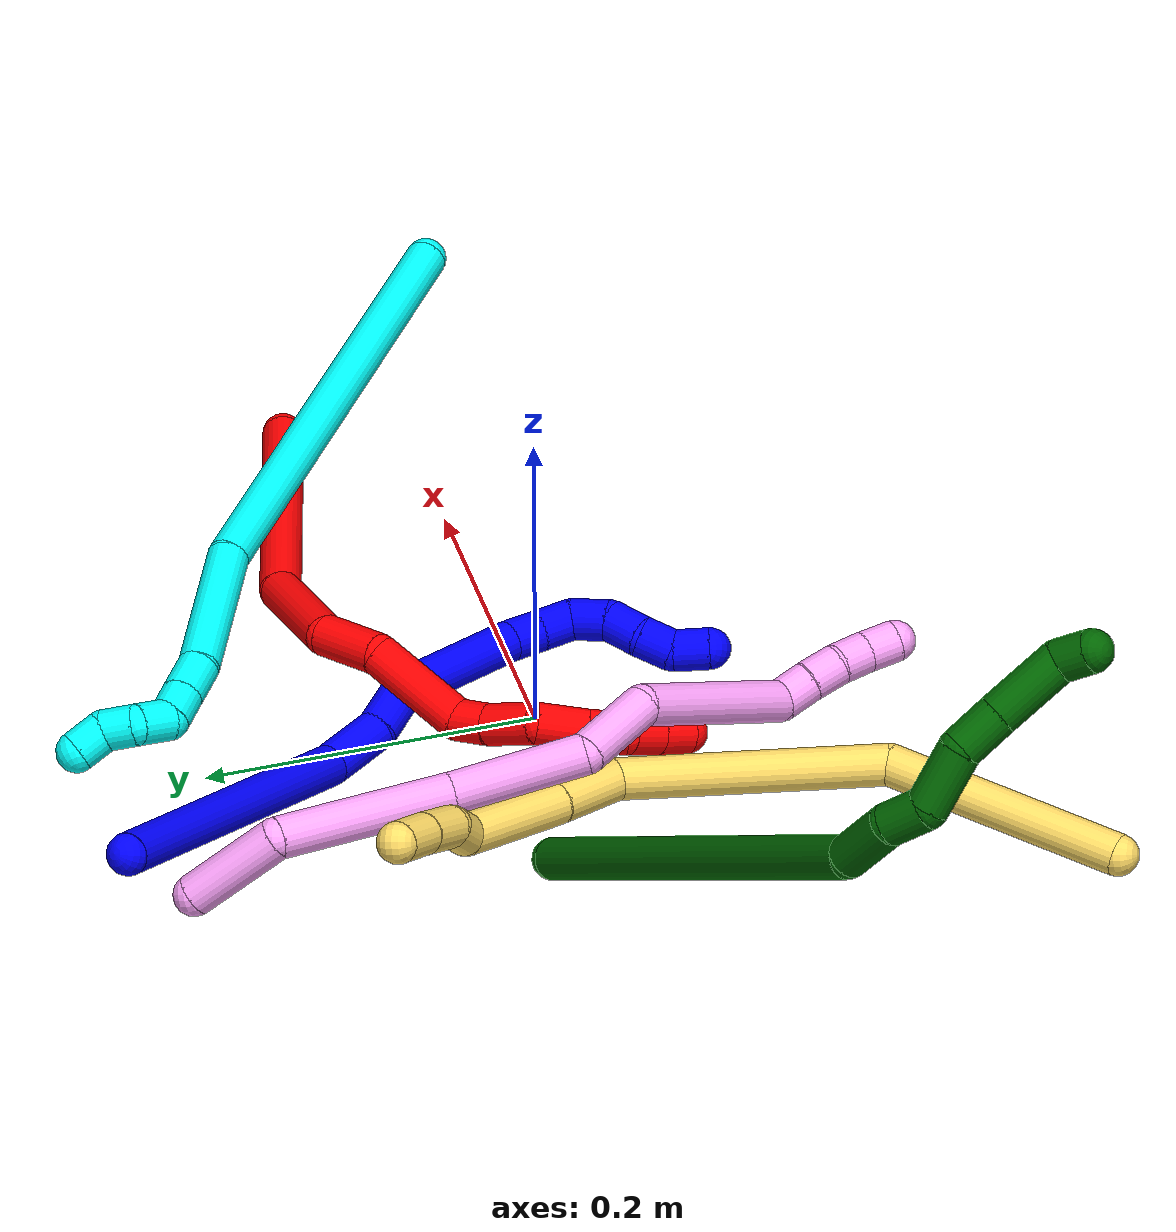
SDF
<sdf version="1.7">
 <world name="default">
  <plugin name="TubeGeneratorPlugin" filename="libtube_generator_plugin.so"/>
  <model name="photoneo_s_sensor">
   <static>1</static>
   <pose>0 0 2 1.57079 1.57079 3.14159</pose>
   <link name="link">
    <inertial><mass>0.1</mass></inertial>
    <sensor name="sensor" type="depth">
     <update_rate>30</update_rate>
     <camera>
      <horizontal_fov>1.22</horizontal_fov>
      <image><width>1920</width><height>1200</height><format>B8G8R8</format></image>
      <clip><near>0.1</near><far>4</far></clip>
      <depth_camera><output>points</output></depth_camera>
     </camera>
     <plugin name="camera_plugin" filename="libgazebo_ros_depth_camera.so">
      <baseline>0.2</baseline>
      <alwaysOn>1</alwaysOn>
      <updateRate>0.0</updateRate>
      <cameraName>camera_ir</cameraName>
      <imageTopicName>/camera/color/image_raw</imageTopicName>
      <cameraInfoTopicName>/camera/color/camera_info</cameraInfoTopicName>
      <depthImageTopicName>/camera/depth/image_raw</depthImageTopicName>
      <depthImageCameraInfoTopicName>/camera/depth/camera_info</depthImageCameraInfoTopicName>
      <pointCloudTopicName>/camera/depth/points</pointCloudTopicName>
      <frameName>fr_optical</frameName>
      <pointCloudCutoff>0.1</pointCloudCutoff>
      <pointCloudCutoffMax>2.0</pointCloudCutoffMax>
      <distortionK1>0</distortionK1>
      <distortionK2>0</distortionK2>
      <distortionK3>0</distortionK3>
      <distortionT1>0</distortionT1>
      <distortionT2>0</distortionT2>
      <CxPrime>0</CxPrime>
      <Cx>0</Cx>
      <Cy>0</Cy>
      <focalLength>0</focalLength>
      <hackBaseline>0</hackBaseline>
     </plugin>
    </sensor>
   </link>
  </model>
  <gravity>0 0 -9.8</gravity>
  <magnetic_field>6e-06 2.3e-05 -4.2e-05</magnetic_field>
  <atmosphere type="adiabatic"/>
  <physics name="default_physics" default="0" type="ode">
   <max_step_size>0.003</max_step_size>
   <real_time_factor>1</real_time_factor>
   <real_time_update_rate>1000</real_time_update_rate>
   <max_contacts>10000</max_contacts>
   <ode>
    <solver>
     <type>quick</type>
     <iters>100</iters>
     <sor>1.3</sor>
     <use_dynamic_moi_rescaling>0</use_dynamic_moi_rescaling>
    </solver>
    <constraints>
     <contact_max_correcting_vel>0</contact_max_correcting_vel>
     <contact_surface_layer>0.001</contact_surface_layer>
     <cfm>0</cfm>
     <erp>0.2</erp>
    </constraints>
   </ode>
  </physics>
  <scene><ambient>0.4 0.4 0.4 1</ambient><background>0.7 0.7 0.7 1</background><shadows>0</shadows></scene>
  <audio><device>default</device></audio>
  <spherical_coordinates>
   <surface_model>EARTH_WGS84</surface_model>
   <latitude_deg>0</latitude_deg>
   <longitude_deg>0</longitude_deg>
   <elevation>0</elevation>
   <heading_deg>0</heading_deg>
  </spherical_coordinates>
  <model name="bin">
   <static>1</static>
   <link name="bottom">
    <collision name="collision-bottom">
     <pose>0 0 -0.01 0 -0 0</pose>
     <geometry><box><size>0.8 0.6 0.02</size></box></geometry>
     <surface>
      <friction><ode><mu>100</mu><mu2>100</mu2></ode></friction>
      <contact><collide_bitmask>65535</collide_bitmask></contact>
     </surface>
    </collision>
   </link>
   <link name="west_wall">
    <collision name="collision-west_wall">
     <pose>-0.41 0 0.1 0 -0 0</pose>
     <geometry><box><size>0.02 0.6 0.2</size></box></geometry>
     <surface>
      <friction><ode><mu>100</mu><mu2>100</mu2></ode></friction>
      <contact><collide_bitmask>65535</collide_bitmask></contact>
     </surface>
    </collision>
   </link>
   <link name="east_wall">
    <collision name="collision-east_wall">
     <pose>0.41 0 0.1 0 -0 0</pose>
     <geometry><box><size>0.02 0.6 0.2</size></box></geometry>
     <surface>
      <friction><ode><mu>100</mu><mu2>100</mu2></ode></friction>
      <contact><collide_bitmask>65535</collide_bitmask></contact>
     </surface>
    </collision>
   </link>
   <link name="south_wall">
    <collision name="collision-south_wall">
     <pose>0 -0.31 0.1 0 -0 0</pose>
     <geometry><box><size>0.8 0.02 0.2</size></box></geometry>
     <surface>
      <friction><ode><mu>100</mu><mu2>100</mu2></ode></friction>
      <contact><collide_bitmask>65535</collide_bitmask></contact>
     </surface>
    </collision>
   </link>
   <link name="north_wall">
    <collision name="collision-north_wall">
     <pose>0 0.31 0.1 0 -0 0</pose>
     <geometry><box><size>0.8 0.02 0.2</size></box></geometry>
     <surface>
      <friction><ode><mu>100</mu><mu2>100</mu2></ode></friction>
      <contact><collide_bitmask>65535</collide_bitmask></contact>
     </surface>
    </collision>
   </link>
  </model>
  <model name="1">
   <static>0</static>
   <link name="1">
    <collision name="collision-cylinder-e_1_1_4">
     <pose>0.025068 0.01113 -0.103109 -3.03406 0.237165 -2.29305</pose>
     <geometry><cylinder><radius>0.0125</radius><length>0.21339</length></cylinder></geometry>
     <surface>
      <friction><ode><mu>1.16</mu><mu2>1.16</mu2><slip1>0</slip1><slip2>0</slip2></ode></friction>
      <contact><ode><kp>1e+06</kp><kd>1</kd><max_vel>0</max_vel><min_depth>0.001</min_depth></ode></contact>
     </surface>
    </collision>
    <visual name="visual-cylinder-e_1_1_4">
     <pose>0.025068 0.01113 -0.103109 -3.03406 0.237165 -2.29305</pose>
     <geometry><cylinder><radius>0.0125</radius><length>0.21339</length></cylinder></geometry>
     <material><ambient>0 0 1 1</ambient></material>
    </visual>
    <collision name="collision-cylinder-e_2_4_5">
     <pose>0.061311 0.018172 -0.221663 2.8828 0.61039 2.35821</pose>
     <geometry><cylinder><radius>0.0125</radius><length>0.038996</length></cylinder></geometry>
     <surface>
      <friction><ode><mu>1.16</mu><mu2>1.16</mu2><slip1>0</slip1><slip2>0</slip2></ode></friction>
      <contact><ode><kp>1e+06</kp><kd>1</kd><max_vel>0</max_vel><min_depth>0.001</min_depth></ode></contact>
     </surface>
    </collision>
    <visual name="visual-cylinder-e_2_4_5">
     <pose>0.061311 0.018172 -0.221663 2.8828 0.61039 2.35821</pose>
     <geometry><cylinder><radius>0.0125</radius><length>0.038996</length></cylinder></geometry>
     <material><ambient>0 0 1 1</ambient></material>
    </visual>
    <collision name="collision-cylinder-e_3_5_6">
     <pose>0.084318 0.013975 -0.247639 3.13132 0.843456 3.1187</pose>
     <geometry><cylinder><radius>0.0125</radius><length>0.031678</length></cylinder></geometry>
     <surface>
      <friction><ode><mu>1.16</mu><mu2>1.16</mu2><slip1>0</slip1><slip2>0</slip2></ode></friction>
      <contact><ode><kp>1e+06</kp><kd>1</kd><max_vel>0</max_vel><min_depth>0.001</min_depth></ode></contact>
     </surface>
    </collision>
    <visual name="visual-cylinder-e_3_5_6">
     <pose>0.084318 0.013975 -0.247639 3.13132 0.843456 3.1187</pose>
     <geometry><cylinder><radius>0.0125</radius><length>0.031678</length></cylinder></geometry>
     <material><ambient>0 0 1 1</ambient></material>
    </visual>
    <collision name="collision-cylinder-e_4_6_7">
     <pose>0.112217 0.006322 -0.296809 2.94876 0.387498 2.22567</pose>
     <geometry><cylinder><radius>0.0125</radius><length>0.085043</length></cylinder></geometry>
     <surface>
      <friction><ode><mu>1.16</mu><mu2>1.16</mu2><slip1>0</slip1><slip2>0</slip2></ode></friction>
      <contact><ode><kp>1e+06</kp><kd>1</kd><max_vel>0</max_vel><min_depth>0.001</min_depth></ode></contact>
     </surface>
    </collision>
    <visual name="visual-cylinder-e_4_6_7">
     <pose>0.112217 0.006322 -0.296809 2.94876 0.387498 2.22567</pose>
     <geometry><cylinder><radius>0.0125</radius><length>0.085043</length></cylinder></geometry>
     <material><ambient>0 0 1 1</ambient></material>
    </visual>
    <collision name="collision-cylinder-e_5_7_8">
     <pose>0.132085 -0.005477 -0.344174 2.68787 0.373166 1.37101</pose>
     <geometry><cylinder><radius>0.0125</radius><length>0.020852</length></cylinder></geometry>
     <surface>
      <friction><ode><mu>1.16</mu><mu2>1.16</mu2><slip1>0</slip1><slip2>0</slip2></ode></friction>
      <contact><ode><kp>1e+06</kp><kd>1</kd><max_vel>0</max_vel><min_depth>0.001</min_depth></ode></contact>
     </surface>
    </collision>
    <visual name="visual-cylinder-e_5_7_8">
     <pose>0.132085 -0.005477 -0.344174 2.68787 0.373166 1.37101</pose>
     <geometry><cylinder><radius>0.0125</radius><length>0.020852</length></cylinder></geometry>
     <material><ambient>0 0 1 1</ambient></material>
    </visual>
    <collision name="collision-cylinder-e_6_8_9">
     <pose>0.140308 -0.015708 -0.360782 2.49295 0.420351 1.13086</pose>
     <geometry><cylinder><radius>0.0125</radius><length>0.021668</length></cylinder></geometry>
     <surface>
      <friction><ode><mu>1.16</mu><mu2>1.16</mu2><slip1>0</slip1><slip2>0</slip2></ode></friction>
      <contact><ode><kp>1e+06</kp><kd>1</kd><max_vel>0</max_vel><min_depth>0.001</min_depth></ode></contact>
     </surface>
    </collision>
    <visual name="visual-cylinder-e_6_8_9">
     <pose>0.140308 -0.015708 -0.360782 2.49295 0.420351 1.13086</pose>
     <geometry><cylinder><radius>0.0125</radius><length>0.021668</length></cylinder></geometry>
     <material><ambient>0 0 1 1</ambient></material>
    </visual>
    <collision name="collision-cylinder-e_7_9_10">
     <pose>0.145685 -0.032842 -0.372631 1.91233 0.080586 0.114108</pose>
     <geometry><cylinder><radius>0.0125</radius><length>0.023763</length></cylinder></geometry>
     <surface>
      <friction><ode><mu>1.16</mu><mu2>1.16</mu2><slip1>0</slip1><slip2>0</slip2></ode></friction>
      <contact><ode><kp>1e+06</kp><kd>1</kd><max_vel>0</max_vel><min_depth>0.001</min_depth></ode></contact>
     </surface>
    </collision>
    <visual name="visual-cylinder-e_7_9_10">
     <pose>0.145685 -0.032842 -0.372631 1.91233 0.080586 0.114108</pose>
     <geometry><cylinder><radius>0.0125</radius><length>0.023763</length></cylinder></geometry>
     <material><ambient>0 0 1 1</ambient></material>
    </visual>
    <collision name="collision-cylinder-e_8_10_11">
     <pose>0.14309 -0.054128 -0.378788 1.78387 -0.330217 -0.407334</pose>
     <geometry><cylinder><radius>0.0125</radius><length>0.021907</length></cylinder></geometry>
     <surface>
      <friction><ode><mu>1.16</mu><mu2>1.16</mu2><slip1>0</slip1><slip2>0</slip2></ode></friction>
      <contact><ode><kp>1e+06</kp><kd>1</kd><max_vel>0</max_vel><min_depth>0.001</min_depth></ode></contact>
     </surface>
    </collision>
    <visual name="visual-cylinder-e_8_10_11">
     <pose>0.14309 -0.054128 -0.378788 1.78387 -0.330217 -0.407334</pose>
     <geometry><cylinder><radius>0.0125</radius><length>0.021907</length></cylinder></geometry>
     <material><ambient>0 0 1 1</ambient></material>
    </visual>
    <collision name="collision-cylinder-e_9_11_12">
     <pose>0.136457 -0.073013 -0.385589 2.05531 -0.301888 -0.493615</pose>
     <geometry><cylinder><radius>0.0125</radius><length>0.020731</length></cylinder></geometry>
     <surface>
      <friction><ode><mu>1.16</mu><mu2>1.16</mu2><slip1>0</slip1><slip2>0</slip2></ode></friction>
      <contact><ode><kp>1e+06</kp><kd>1</kd><max_vel>0</max_vel><min_depth>0.001</min_depth></ode></contact>
     </surface>
    </collision>
    <visual name="visual-cylinder-e_9_11_12">
     <pose>0.136457 -0.073013 -0.385589 2.05531 -0.301888 -0.493615</pose>
     <geometry><cylinder><radius>0.0125</radius><length>0.020731</length></cylinder></geometry>
     <material><ambient>0 0 1 1</ambient></material>
    </visual>
    <collision name="collision-cylinder-e_10_12_2">
     <pose>0.13519 -0.090791 -0.396201 2.15794 0.165991 0.308089</pose>
     <geometry><cylinder><radius>0.0125</radius><length>0.021974</length></cylinder></geometry>
     <surface>
      <friction><ode><mu>1.16</mu><mu2>1.16</mu2><slip1>0</slip1><slip2>0</slip2></ode></friction>
      <contact><ode><kp>1e+06</kp><kd>1</kd><max_vel>0</max_vel><min_depth>0.001</min_depth></ode></contact>
     </surface>
    </collision>
    <visual name="visual-cylinder-e_10_12_2">
     <pose>0.13519 -0.090791 -0.396201 2.15794 0.165991 0.308089</pose>
     <geometry><cylinder><radius>0.0125</radius><length>0.021974</length></cylinder></geometry>
     <material><ambient>0 0 1 1</ambient></material>
    </visual>
    <collision name="collision-sphere-2">
     <pose>0.137005 -0.099812 -0.402204 0 -0 0</pose>
     <geometry><sphere><radius>0.0125</radius></sphere></geometry>
     <surface>
      <friction><ode><mu>1.16</mu><mu2>1.16</mu2><slip1>0</slip1><slip2>0</slip2></ode></friction>
      <contact><ode><kp>1e+06</kp><kd>1</kd><max_vel>0</max_vel><min_depth>0.001</min_depth></ode></contact>
     </surface>
    </collision>
    <visual name="visual-sphere-2">
     <pose>0.137005 -0.099812 -0.402204 0 -0 0</pose>
     <geometry><sphere><radius>0.0125</radius></sphere></geometry>
     <material><ambient>0 0 1 1</ambient></material>
    </visual>
    <collision name="collision-sphere-12">
     <pose>0.133375 -0.08177 -0.390198 0 -0 0</pose>
     <geometry><sphere><radius>0.0125</radius></sphere></geometry>
     <surface>
      <friction><ode><mu>1.16</mu><mu2>1.16</mu2><slip1>0</slip1><slip2>0</slip2></ode></friction>
      <contact><ode><kp>1e+06</kp><kd>1</kd><max_vel>0</max_vel><min_depth>0.001</min_depth></ode></contact>
     </surface>
    </collision>
    <visual name="visual-sphere-12">
     <pose>0.133375 -0.08177 -0.390198 0 -0 0</pose>
     <geometry><sphere><radius>0.0125</radius></sphere></geometry>
     <material><ambient>0 0 1 1</ambient></material>
    </visual>
    <collision name="collision-sphere-11">
     <pose>0.139538 -0.064255 -0.380979 0 -0 0</pose>
     <geometry><sphere><radius>0.0125</radius></sphere></geometry>
     <surface>
      <friction><ode><mu>1.16</mu><mu2>1.16</mu2><slip1>0</slip1><slip2>0</slip2></ode></friction>
      <contact><ode><kp>1e+06</kp><kd>1</kd><max_vel>0</max_vel><min_depth>0.001</min_depth></ode></contact>
     </surface>
    </collision>
    <visual name="visual-sphere-11">
     <pose>0.139538 -0.064255 -0.380979 0 -0 0</pose>
     <geometry><sphere><radius>0.0125</radius></sphere></geometry>
     <material><ambient>0 0 1 1</ambient></material>
    </visual>
    <collision name="collision-sphere-10">
     <pose>0.146642 -0.044001 -0.376597 0 -0 0</pose>
     <geometry><sphere><radius>0.0125</radius></sphere></geometry>
     <surface>
      <friction><ode><mu>1.16</mu><mu2>1.16</mu2><slip1>0</slip1><slip2>0</slip2></ode></friction>
      <contact><ode><kp>1e+06</kp><kd>1</kd><max_vel>0</max_vel><min_depth>0.001</min_depth></ode></contact>
     </surface>
    </collision>
    <visual name="visual-sphere-10">
     <pose>0.146642 -0.044001 -0.376597 0 -0 0</pose>
     <geometry><sphere><radius>0.0125</radius></sphere></geometry>
     <material><ambient>0 0 1 1</ambient></material>
    </visual>
    <collision name="collision-sphere-9">
     <pose>0.144729 -0.021683 -0.368664 0 -0 0</pose>
     <geometry><sphere><radius>0.0125</radius></sphere></geometry>
     <surface>
      <friction><ode><mu>1.16</mu><mu2>1.16</mu2><slip1>0</slip1><slip2>0</slip2></ode></friction>
      <contact><ode><kp>1e+06</kp><kd>1</kd><max_vel>0</max_vel><min_depth>0.001</min_depth></ode></contact>
     </surface>
    </collision>
    <visual name="visual-sphere-9">
     <pose>0.144729 -0.021683 -0.368664 0 -0 0</pose>
     <geometry><sphere><radius>0.0125</radius></sphere></geometry>
     <material><ambient>0 0 1 1</ambient></material>
    </visual>
    <collision name="collision-sphere-4">
     <pose>0.050135 0.02226 -0.206218 0 -0 0</pose>
     <geometry><sphere><radius>0.0125</radius></sphere></geometry>
     <surface>
      <friction><ode><mu>1.16</mu><mu2>1.16</mu2><slip1>0</slip1><slip2>0</slip2></ode></friction>
      <contact><ode><kp>1e+06</kp><kd>1</kd><max_vel>0</max_vel><min_depth>0.001</min_depth></ode></contact>
     </surface>
    </collision>
    <visual name="visual-sphere-4">
     <pose>0.050135 0.02226 -0.206218 0 -0 0</pose>
     <geometry><sphere><radius>0.0125</radius></sphere></geometry>
     <material><ambient>0 0 1 1</ambient></material>
    </visual>
    <collision name="collision-sphere-1">
     <geometry><sphere><radius>0.0125</radius></sphere></geometry>
     <surface>
      <friction><ode><mu>1.16</mu><mu2>1.16</mu2><slip1>0</slip1><slip2>0</slip2></ode></friction>
      <contact><ode><kp>1e+06</kp><kd>1</kd><max_vel>0</max_vel><min_depth>0.001</min_depth></ode></contact>
     </surface>
    </collision>
    <visual name="visual-sphere-1">
     <geometry><sphere><radius>0.0125</radius></sphere></geometry>
     <material><ambient>0 0 1 1</ambient></material>
    </visual>
    <collision name="collision-sphere-8">
     <pose>0.135886 -0.009733 -0.3529 0 -0 0</pose>
     <geometry><sphere><radius>0.0125</radius></sphere></geometry>
     <surface>
      <friction><ode><mu>1.16</mu><mu2>1.16</mu2><slip1>0</slip1><slip2>0</slip2></ode></friction>
      <contact><ode><kp>1e+06</kp><kd>1</kd><max_vel>0</max_vel><min_depth>0.001</min_depth></ode></contact>
     </surface>
    </collision>
    <visual name="visual-sphere-8">
     <pose>0.135886 -0.009733 -0.3529 0 -0 0</pose>
     <geometry><sphere><radius>0.0125</radius></sphere></geometry>
     <material><ambient>0 0 1 1</ambient></material>
    </visual>
    <collision name="collision-sphere-5">
     <pose>0.072487 0.014083 -0.237109 0 -0 0</pose>
     <geometry><sphere><radius>0.0125</radius></sphere></geometry>
     <surface>
      <friction><ode><mu>1.16</mu><mu2>1.16</mu2><slip1>0</slip1><slip2>0</slip2></ode></friction>
      <contact><ode><kp>1e+06</kp><kd>1</kd><max_vel>0</max_vel><min_depth>0.001</min_depth></ode></contact>
     </surface>
    </collision>
    <visual name="visual-sphere-5">
     <pose>0.072487 0.014083 -0.237109 0 -0 0</pose>
     <geometry><sphere><radius>0.0125</radius></sphere></geometry>
     <material><ambient>0 0 1 1</ambient></material>
    </visual>
    <collision name="collision-sphere-6">
     <pose>0.096149 0.013867 -0.25817 0 -0 0</pose>
     <geometry><sphere><radius>0.0125</radius></sphere></geometry>
     <surface>
      <friction><ode><mu>1.16</mu><mu2>1.16</mu2><slip1>0</slip1><slip2>0</slip2></ode></friction>
      <contact><ode><kp>1e+06</kp><kd>1</kd><max_vel>0</max_vel><min_depth>0.001</min_depth></ode></contact>
     </surface>
    </collision>
    <visual name="visual-sphere-6">
     <pose>0.096149 0.013867 -0.25817 0 -0 0</pose>
     <geometry><sphere><radius>0.0125</radius></sphere></geometry>
     <material><ambient>0 0 1 1</ambient></material>
    </visual>
    <collision name="collision-sphere-7">
     <pose>0.128285 -0.001222 -0.335448 0 -0 0</pose>
     <geometry><sphere><radius>0.0125</radius></sphere></geometry>
     <surface>
      <friction><ode><mu>1.16</mu><mu2>1.16</mu2><slip1>0</slip1><slip2>0</slip2></ode></friction>
      <contact><ode><kp>1e+06</kp><kd>1</kd><max_vel>0</max_vel><min_depth>0.001</min_depth></ode></contact>
     </surface>
    </collision>
    <visual name="visual-sphere-7">
     <pose>0.128285 -0.001222 -0.335448 0 -0 0</pose>
     <geometry><sphere><radius>0.0125</radius></sphere></geometry>
     <material><ambient>0 0 1 1</ambient></material>
    </visual>
    <inertial>
     <pose>0.076289 -0.003731 -0.225158 0 -0 0</pose>
     <mass>0.5</mass>
     <inertia>
      <ixx>-0.001095</ixx>
      <ixy>0</ixy>
      <ixz>0</ixz>
      <iyy>3.7e-05</iyy>
      <iyz>0</iyz>
      <izz>-0.000318</izz>
     </inertia>
    </inertial>
   </link>
   <pose>-0.153646 0.281423 0.084327 -0.48324 -0.942554 -0.463103</pose>
  </model>
  <model name="2">
   <static>0</static>
   <link name="2">
    <collision name="collision-cylinder-e_1_1_4">
     <pose>-0.07181 -0.048178 -0.014225 1.85789 -0.960376 -1.21723</pose>
     <geometry><cylinder><radius>0.0125</radius><length>0.175272</length></cylinder></geometry>
     <surface>
      <friction><ode><mu>1.16</mu><mu2>1.16</mu2><slip1>0</slip1><slip2>0</slip2></ode></friction>
      <contact><ode><kp>1e+06</kp><kd>1</kd><max_vel>0</max_vel><min_depth>0.001</min_depth></ode></contact>
     </surface>
    </collision>
    <visual name="visual-cylinder-e_1_1_4">
     <pose>-0.07181 -0.048178 -0.014225 1.85789 -0.960376 -1.21723</pose>
     <geometry><cylinder><radius>0.0125</radius><length>0.175272</length></cylinder></geometry>
     <material><ambient>1 0 0 1</ambient></material>
    </visual>
    <collision name="collision-cylinder-e_2_4_5">
     <pose>-0.174543 -0.114447 -0.01934 1.10432 -0.990923 -0.642801</pose>
     <geometry><cylinder><radius>0.0125</radius><length>0.073935</length></cylinder></geometry>
     <surface>
      <friction><ode><mu>1.16</mu><mu2>1.16</mu2><slip1>0</slip1><slip2>0</slip2></ode></friction>
      <contact><ode><kp>1e+06</kp><kd>1</kd><max_vel>0</max_vel><min_depth>0.001</min_depth></ode></contact>
     </surface>
    </collision>
    <visual name="visual-cylinder-e_2_4_5">
     <pose>-0.174543 -0.114447 -0.01934 1.10432 -0.990923 -0.642801</pose>
     <geometry><cylinder><radius>0.0125</radius><length>0.073935</length></cylinder></geometry>
     <material><ambient>1 0 0 1</ambient></material>
    </visual>
    <collision name="collision-cylinder-e_3_5_6">
     <pose>-0.21734 -0.143225 0.002803 0.686822 -0.61366 -0.225626</pose>
     <geometry><cylinder><radius>0.0125</radius><length>0.041232</length></cylinder></geometry>
     <surface>
      <friction><ode><mu>1.16</mu><mu2>1.16</mu2><slip1>0</slip1><slip2>0</slip2></ode></friction>
      <contact><ode><kp>1e+06</kp><kd>1</kd><max_vel>0</max_vel><min_depth>0.001</min_depth></ode></contact>
     </surface>
    </collision>
    <visual name="visual-cylinder-e_3_5_6">
     <pose>-0.21734 -0.143225 0.002803 0.686822 -0.61366 -0.225626</pose>
     <geometry><cylinder><radius>0.0125</radius><length>0.041232</length></cylinder></geometry>
     <material><ambient>1 0 0 1</ambient></material>
    </visual>
    <collision name="collision-cylinder-e_4_6_7">
     <pose>-0.236324 -0.179598 0.03181 1.01443 -0.230944 -0.128734</pose>
     <geometry><cylinder><radius>0.0125</radius><length>0.062145</length></cylinder></geometry>
     <surface>
      <friction><ode><mu>1.16</mu><mu2>1.16</mu2><slip1>0</slip1><slip2>0</slip2></ode></friction>
      <contact><ode><kp>1e+06</kp><kd>1</kd><max_vel>0</max_vel><min_depth>0.001</min_depth></ode></contact>
     </surface>
    </collision>
    <visual name="visual-cylinder-e_4_6_7">
     <pose>-0.236324 -0.179598 0.03181 1.01443 -0.230944 -0.128734</pose>
     <geometry><cylinder><radius>0.0125</radius><length>0.062145</length></cylinder></geometry>
     <material><ambient>1 0 0 1</ambient></material>
    </visual>
    <collision name="collision-cylinder-e_5_7_8">
     <pose>-0.248273 -0.20965 0.055991 0.488926 -0.479666 -0.121851</pose>
     <geometry><cylinder><radius>0.0125</radius><length>0.020959</length></cylinder></geometry>
     <surface>
      <friction><ode><mu>1.16</mu><mu2>1.16</mu2><slip1>0</slip1><slip2>0</slip2></ode></friction>
      <contact><ode><kp>1e+06</kp><kd>1</kd><max_vel>0</max_vel><min_depth>0.001</min_depth></ode></contact>
     </surface>
    </collision>
    <visual name="visual-cylinder-e_5_7_8">
     <pose>-0.248273 -0.20965 0.055991 0.488926 -0.479666 -0.121851</pose>
     <geometry><cylinder><radius>0.0125</radius><length>0.020959</length></cylinder></geometry>
     <material><ambient>1 0 0 1</ambient></material>
    </visual>
    <collision name="collision-cylinder-e_6_8_9">
     <pose>-0.261177 -0.218237 0.077284 0.311979 -0.530653 -0.085417</pose>
     <geometry><cylinder><radius>0.0125</radius><length>0.031883</length></cylinder></geometry>
     <surface>
      <friction><ode><mu>1.16</mu><mu2>1.16</mu2><slip1>0</slip1><slip2>0</slip2></ode></friction>
      <contact><ode><kp>1e+06</kp><kd>1</kd><max_vel>0</max_vel><min_depth>0.001</min_depth></ode></contact>
     </surface>
    </collision>
    <visual name="visual-cylinder-e_6_8_9">
     <pose>-0.261177 -0.218237 0.077284 0.311979 -0.530653 -0.085417</pose>
     <geometry><cylinder><radius>0.0125</radius><length>0.031883</length></cylinder></geometry>
     <material><ambient>1 0 0 1</ambient></material>
    </visual>
    <collision name="collision-cylinder-e_7_9_10">
     <pose>-0.267709 -0.229042 0.103723 0.458118 0.10275 0.023976</pose>
     <geometry><cylinder><radius>0.0125</radius><length>0.029936</length></cylinder></geometry>
     <surface>
      <friction><ode><mu>1.16</mu><mu2>1.16</mu2><slip1>0</slip1><slip2>0</slip2></ode></friction>
      <contact><ode><kp>1e+06</kp><kd>1</kd><max_vel>0</max_vel><min_depth>0.001</min_depth></ode></contact>
     </surface>
    </collision>
    <visual name="visual-cylinder-e_7_9_10">
     <pose>-0.267709 -0.229042 0.103723 0.458118 0.10275 0.023976</pose>
     <geometry><cylinder><radius>0.0125</radius><length>0.029936</length></cylinder></geometry>
     <material><ambient>1 0 0 1</ambient></material>
    </visual>
    <collision name="collision-cylinder-e_8_10_11">
     <pose>-0.264929 -0.240303 0.127917 0.40728 0.10504 0.02171</pose>
     <geometry><cylinder><radius>0.0125</radius><length>0.023741</length></cylinder></geometry>
     <surface>
      <friction><ode><mu>1.16</mu><mu2>1.16</mu2><slip1>0</slip1><slip2>0</slip2></ode></friction>
      <contact><ode><kp>1e+06</kp><kd>1</kd><max_vel>0</max_vel><min_depth>0.001</min_depth></ode></contact>
     </surface>
    </collision>
    <visual name="visual-cylinder-e_8_10_11">
     <pose>-0.264929 -0.240303 0.127917 0.40728 0.10504 0.02171</pose>
     <geometry><cylinder><radius>0.0125</radius><length>0.023741</length></cylinder></geometry>
     <material><ambient>1 0 0 1</ambient></material>
    </visual>
    <collision name="collision-cylinder-e_9_11_12">
     <pose>-0.25796 -0.247582 0.146768 0.314098 0.596896 0.097353</pose>
     <geometry><cylinder><radius>0.0125</radius><length>0.020369</length></cylinder></geometry>
     <surface>
      <friction><ode><mu>1.16</mu><mu2>1.16</mu2><slip1>0</slip1><slip2>0</slip2></ode></friction>
      <contact><ode><kp>1e+06</kp><kd>1</kd><max_vel>0</max_vel><min_depth>0.001</min_depth></ode></contact>
     </surface>
    </collision>
    <visual name="visual-cylinder-e_9_11_12">
     <pose>-0.25796 -0.247582 0.146768 0.314098 0.596896 0.097353</pose>
     <geometry><cylinder><radius>0.0125</radius><length>0.020369</length></cylinder></geometry>
     <material><ambient>1 0 0 1</ambient></material>
    </visual>
    <collision name="collision-cylinder-e_10_12_2">
     <pose>-0.246673 -0.25249 0.163091 0.270608 0.572755 0.080133</pose>
     <geometry><cylinder><radius>0.0125</radius><length>0.020528</length></cylinder></geometry>
     <surface>
      <friction><ode><mu>1.16</mu><mu2>1.16</mu2><slip1>0</slip1><slip2>0</slip2></ode></friction>
      <contact><ode><kp>1e+06</kp><kd>1</kd><max_vel>0</max_vel><min_depth>0.001</min_depth></ode></contact>
     </surface>
    </collision>
    <visual name="visual-cylinder-e_10_12_2">
     <pose>-0.246673 -0.25249 0.163091 0.270608 0.572755 0.080133</pose>
     <geometry><cylinder><radius>0.0125</radius><length>0.020528</length></cylinder></geometry>
     <material><ambient>1 0 0 1</ambient></material>
    </visual>
    <collision name="collision-sphere-2">
     <pose>-0.241111 -0.254796 0.171403 0 -0 0</pose>
     <geometry><sphere><radius>0.0125</radius></sphere></geometry>
     <surface>
      <friction><ode><mu>1.16</mu><mu2>1.16</mu2><slip1>0</slip1><slip2>0</slip2></ode></friction>
      <contact><ode><kp>1e+06</kp><kd>1</kd><max_vel>0</max_vel><min_depth>0.001</min_depth></ode></contact>
     </surface>
    </collision>
    <visual name="visual-sphere-2">
     <pose>-0.241111 -0.254796 0.171403 0 -0 0</pose>
     <geometry><sphere><radius>0.0125</radius></sphere></geometry>
     <material><ambient>1 0 0 1</ambient></material>
    </visual>
    <collision name="collision-sphere-12">
     <pose>-0.252236 -0.250184 0.154779 0 -0 0</pose>
     <geometry><sphere><radius>0.0125</radius></sphere></geometry>
     <surface>
      <friction><ode><mu>1.16</mu><mu2>1.16</mu2><slip1>0</slip1><slip2>0</slip2></ode></friction>
      <contact><ode><kp>1e+06</kp><kd>1</kd><max_vel>0</max_vel><min_depth>0.001</min_depth></ode></contact>
     </surface>
    </collision>
    <visual name="visual-sphere-12">
     <pose>-0.252236 -0.250184 0.154779 0 -0 0</pose>
     <geometry><sphere><radius>0.0125</radius></sphere></geometry>
     <material><ambient>1 0 0 1</ambient></material>
    </visual>
    <collision name="collision-sphere-11">
     <pose>-0.263685 -0.244979 0.138756 0 -0 0</pose>
     <geometry><sphere><radius>0.0125</radius></sphere></geometry>
     <surface>
      <friction><ode><mu>1.16</mu><mu2>1.16</mu2><slip1>0</slip1><slip2>0</slip2></ode></friction>
      <contact><ode><kp>1e+06</kp><kd>1</kd><max_vel>0</max_vel><min_depth>0.001</min_depth></ode></contact>
     </surface>
    </collision>
    <visual name="visual-sphere-11">
     <pose>-0.263685 -0.244979 0.138756 0 -0 0</pose>
     <geometry><sphere><radius>0.0125</radius></sphere></geometry>
     <material><ambient>1 0 0 1</ambient></material>
    </visual>
    <collision name="collision-sphere-10">
     <pose>-0.266174 -0.235627 0.117077 0 -0 0</pose>
     <geometry><sphere><radius>0.0125</radius></sphere></geometry>
     <surface>
      <friction><ode><mu>1.16</mu><mu2>1.16</mu2><slip1>0</slip1><slip2>0</slip2></ode></friction>
      <contact><ode><kp>1e+06</kp><kd>1</kd><max_vel>0</max_vel><min_depth>0.001</min_depth></ode></contact>
     </surface>
    </collision>
    <visual name="visual-sphere-10">
     <pose>-0.266174 -0.235627 0.117077 0 -0 0</pose>
     <geometry><sphere><radius>0.0125</radius></sphere></geometry>
     <material><ambient>1 0 0 1</ambient></material>
    </visual>
    <collision name="collision-sphere-9">
     <pose>-0.269245 -0.222457 0.090369 0 -0 0</pose>
     <geometry><sphere><radius>0.0125</radius></sphere></geometry>
     <surface>
      <friction><ode><mu>1.16</mu><mu2>1.16</mu2><slip1>0</slip1><slip2>0</slip2></ode></friction>
      <contact><ode><kp>1e+06</kp><kd>1</kd><max_vel>0</max_vel><min_depth>0.001</min_depth></ode></contact>
     </surface>
    </collision>
    <visual name="visual-sphere-9">
     <pose>-0.269245 -0.222457 0.090369 0 -0 0</pose>
     <geometry><sphere><radius>0.0125</radius></sphere></geometry>
     <material><ambient>1 0 0 1</ambient></material>
    </visual>
    <collision name="collision-sphere-4">
     <pose>-0.143619 -0.096356 -0.028449 0 -0 0</pose>
     <geometry><sphere><radius>0.0125</radius></sphere></geometry>
     <surface>
      <friction><ode><mu>1.16</mu><mu2>1.16</mu2><slip1>0</slip1><slip2>0</slip2></ode></friction>
      <contact><ode><kp>1e+06</kp><kd>1</kd><max_vel>0</max_vel><min_depth>0.001</min_depth></ode></contact>
     </surface>
    </collision>
    <visual name="visual-sphere-4">
     <pose>-0.143619 -0.096356 -0.028449 0 -0 0</pose>
     <geometry><sphere><radius>0.0125</radius></sphere></geometry>
     <material><ambient>1 0 0 1</ambient></material>
    </visual>
    <collision name="collision-sphere-1">
     <geometry><sphere><radius>0.0125</radius></sphere></geometry>
     <surface>
      <friction><ode><mu>1.16</mu><mu2>1.16</mu2><slip1>0</slip1><slip2>0</slip2></ode></friction>
      <contact><ode><kp>1e+06</kp><kd>1</kd><max_vel>0</max_vel><min_depth>0.001</min_depth></ode></contact>
     </surface>
    </collision>
    <visual name="visual-sphere-1">
     <geometry><sphere><radius>0.0125</radius></sphere></geometry>
     <material><ambient>1 0 0 1</ambient></material>
    </visual>
    <collision name="collision-sphere-8">
     <pose>-0.253109 -0.214017 0.064199 0 -0 0</pose>
     <geometry><sphere><radius>0.0125</radius></sphere></geometry>
     <surface>
      <friction><ode><mu>1.16</mu><mu2>1.16</mu2><slip1>0</slip1><slip2>0</slip2></ode></friction>
      <contact><ode><kp>1e+06</kp><kd>1</kd><max_vel>0</max_vel><min_depth>0.001</min_depth></ode></contact>
     </surface>
    </collision>
    <visual name="visual-sphere-8">
     <pose>-0.253109 -0.214017 0.064199 0 -0 0</pose>
     <geometry><sphere><radius>0.0125</radius></sphere></geometry>
     <material><ambient>1 0 0 1</ambient></material>
    </visual>
    <collision name="collision-sphere-5">
     <pose>-0.205468 -0.132538 -0.01023 0 -0 0</pose>
     <geometry><sphere><radius>0.0125</radius></sphere></geometry>
     <surface>
      <friction><ode><mu>1.16</mu><mu2>1.16</mu2><slip1>0</slip1><slip2>0</slip2></ode></friction>
      <contact><ode><kp>1e+06</kp><kd>1</kd><max_vel>0</max_vel><min_depth>0.001</min_depth></ode></contact>
     </surface>
    </collision>
    <visual name="visual-sphere-5">
     <pose>-0.205468 -0.132538 -0.01023 0 -0 0</pose>
     <geometry><sphere><radius>0.0125</radius></sphere></geometry>
     <material><ambient>1 0 0 1</ambient></material>
    </visual>
    <collision name="collision-sphere-6">
     <pose>-0.229212 -0.153912 0.015836 0 -0 0</pose>
     <geometry><sphere><radius>0.0125</radius></sphere></geometry>
     <surface>
      <friction><ode><mu>1.16</mu><mu2>1.16</mu2><slip1>0</slip1><slip2>0</slip2></ode></friction>
      <contact><ode><kp>1e+06</kp><kd>1</kd><max_vel>0</max_vel><min_depth>0.001</min_depth></ode></contact>
     </surface>
    </collision>
    <visual name="visual-sphere-6">
     <pose>-0.229212 -0.153912 0.015836 0 -0 0</pose>
     <geometry><sphere><radius>0.0125</radius></sphere></geometry>
     <material><ambient>1 0 0 1</ambient></material>
    </visual>
    <collision name="collision-sphere-7">
     <pose>-0.243437 -0.205283 0.047783 0 -0 0</pose>
     <geometry><sphere><radius>0.0125</radius></sphere></geometry>
     <surface>
      <friction><ode><mu>1.16</mu><mu2>1.16</mu2><slip1>0</slip1><slip2>0</slip2></ode></friction>
      <contact><ode><kp>1e+06</kp><kd>1</kd><max_vel>0</max_vel><min_depth>0.001</min_depth></ode></contact>
     </surface>
    </collision>
    <visual name="visual-sphere-7">
     <pose>-0.243437 -0.205283 0.047783 0 -0 0</pose>
     <geometry><sphere><radius>0.0125</radius></sphere></geometry>
     <material><ambient>1 0 0 1</ambient></material>
    </visual>
    <inertial>
     <pose>-0.174583 -0.136225 0.028573 0 -0 0</pose>
     <mass>0.5</mass>
     <inertia>
      <ixx>-0.000133</ixx>
      <ixy>0</ixy>
      <ixz>0</ixz>
      <iyy>7.1e-05</iyy>
      <iyz>0</iyz>
      <izz>0.000723</izz>
     </inertia>
    </inertial>
   </link>
   <pose>0.29535 0.075791 0.011709 1.24369 0.698873 -0.285822</pose>
  </model>
  <model name="3">
   <static>0</static>
   <link name="3">
    <collision name="collision-cylinder-e_1_1_4">
     <pose>-0.098461 0.048598 0.103965 -0.43727 -0.709089 0.164132</pose>
     <geometry><cylinder><radius>0.0125</radius><length>0.302424</length></cylinder></geometry>
     <surface>
      <friction><ode><mu>1.16</mu><mu2>1.16</mu2><slip1>0</slip1><slip2>0</slip2></ode></friction>
      <contact><ode><kp>1e+06</kp><kd>1</kd><max_vel>0</max_vel><min_depth>0.001</min_depth></ode></contact>
     </surface>
    </collision>
    <visual name="visual-cylinder-e_1_1_4">
     <pose>-0.098461 0.048598 0.103965 -0.43727 -0.709089 0.164132</pose>
     <geometry><cylinder><radius>0.0125</radius><length>0.302424</length></cylinder></geometry>
     <material><ambient>0.003922 1 0.996078 1</ambient></material>
    </visual>
    <collision name="collision-cylinder-e_2_4_5">
     <pose>-0.218106 0.111028 0.245659 -0.351386 -0.485169 0.087803</pose>
     <geometry><cylinder><radius>0.0125</radius><length>0.090854</length></cylinder></geometry>
     <surface>
      <friction><ode><mu>1.16</mu><mu2>1.16</mu2><slip1>0</slip1><slip2>0</slip2></ode></friction>
      <contact><ode><kp>1e+06</kp><kd>1</kd><max_vel>0</max_vel><min_depth>0.001</min_depth></ode></contact>
     </surface>
    </collision>
    <visual name="visual-cylinder-e_2_4_5">
     <pose>-0.218106 0.111028 0.245659 -0.351386 -0.485169 0.087803</pose>
     <geometry><cylinder><radius>0.0125</radius><length>0.090854</length></cylinder></geometry>
     <material><ambient>0.003922 1 0.996078 1</ambient></material>
    </visual>
    <collision name="collision-cylinder-e_3_5_6">
     <pose>-0.247253 0.127792 0.292488 -0.311774 -0.694378 0.113615</pose>
     <geometry><cylinder><radius>0.0125</radius><length>0.024883</length></cylinder></geometry>
     <surface>
      <friction><ode><mu>1.16</mu><mu2>1.16</mu2><slip1>0</slip1><slip2>0</slip2></ode></friction>
      <contact><ode><kp>1e+06</kp><kd>1</kd><max_vel>0</max_vel><min_depth>0.001</min_depth></ode></contact>
     </surface>
    </collision>
    <visual name="visual-cylinder-e_3_5_6">
     <pose>-0.247253 0.127792 0.292488 -0.311774 -0.694378 0.113615</pose>
     <geometry><cylinder><radius>0.0125</radius><length>0.024883</length></cylinder></geometry>
     <material><ambient>0.003922 1 0.996078 1</ambient></material>
    </visual>
    <collision name="collision-cylinder-e_4_6_7">
     <pose>-0.261564 0.133193 0.309077 -0.318335 -0.677982 0.113083</pose>
     <geometry><cylinder><radius>0.0125</radius><length>0.020249</length></cylinder></geometry>
     <surface>
      <friction><ode><mu>1.16</mu><mu2>1.16</mu2><slip1>0</slip1><slip2>0</slip2></ode></friction>
      <contact><ode><kp>1e+06</kp><kd>1</kd><max_vel>0</max_vel><min_depth>0.001</min_depth></ode></contact>
     </surface>
    </collision>
    <visual name="visual-cylinder-e_4_6_7">
     <pose>-0.261564 0.133193 0.309077 -0.318335 -0.677982 0.113083</pose>
     <geometry><cylinder><radius>0.0125</radius><length>0.020249</length></cylinder></geometry>
     <material><ambient>0.003922 1 0.996078 1</ambient></material>
    </visual>
    <collision name="collision-cylinder-e_5_7_8">
     <pose>-0.278216 0.138412 0.317271 -1.31993 -1.30182 1.06766</pose>
     <geometry><cylinder><radius>0.0125</radius><length>0.021372</length></cylinder></geometry>
     <surface>
      <friction><ode><mu>1.16</mu><mu2>1.16</mu2><slip1>0</slip1><slip2>0</slip2></ode></friction>
      <contact><ode><kp>1e+06</kp><kd>1</kd><max_vel>0</max_vel><min_depth>0.001</min_depth></ode></contact>
     </surface>
    </collision>
    <visual name="visual-cylinder-e_5_7_8">
     <pose>-0.278216 0.138412 0.317271 -1.31993 -1.30182 1.06766</pose>
     <geometry><cylinder><radius>0.0125</radius><length>0.021372</length></cylinder></geometry>
     <material><ambient>0.003922 1 0.996078 1</ambient></material>
    </visual>
    <collision name="collision-cylinder-e_6_8_9">
     <pose>-0.297349 0.136727 0.316011 1.98778 -1.06839 -1.47557</pose>
     <geometry><cylinder><radius>0.0125</radius><length>0.020152</length></cylinder></geometry>
     <surface>
      <friction><ode><mu>1.16</mu><mu2>1.16</mu2><slip1>0</slip1><slip2>0</slip2></ode></friction>
      <contact><ode><kp>1e+06</kp><kd>1</kd><max_vel>0</max_vel><min_depth>0.001</min_depth></ode></contact>
     </surface>
    </collision>
    <visual name="visual-cylinder-e_6_8_9">
     <pose>-0.297349 0.136727 0.316011 1.98778 -1.06839 -1.47557</pose>
     <geometry><cylinder><radius>0.0125</radius><length>0.020152</length></cylinder></geometry>
     <material><ambient>0.003922 1 0.996078 1</ambient></material>
    </visual>
    <collision name="collision-cylinder-e_7_9_2">
     <pose>-0.315139 0.129757 0.317785 0.595537 -1.1038 -0.373518</pose>
     <geometry><cylinder><radius>0.0125</radius><length>0.020067</length></cylinder></geometry>
     <surface>
      <friction><ode><mu>1.16</mu><mu2>1.16</mu2><slip1>0</slip1><slip2>0</slip2></ode></friction>
      <contact><ode><kp>1e+06</kp><kd>1</kd><max_vel>0</max_vel><min_depth>0.001</min_depth></ode></contact>
     </surface>
    </collision>
    <visual name="visual-cylinder-e_7_9_2">
     <pose>-0.315139 0.129757 0.317785 0.595537 -1.1038 -0.373518</pose>
     <geometry><cylinder><radius>0.0125</radius><length>0.020067</length></cylinder></geometry>
     <material><ambient>0.003922 1 0.996078 1</ambient></material>
    </visual>
    <collision name="collision-sphere-2">
     <pose>-0.324098 0.127223 0.321524 0 -0 0</pose>
     <geometry><sphere><radius>0.0125</radius></sphere></geometry>
     <surface>
      <friction><ode><mu>1.16</mu><mu2>1.16</mu2><slip1>0</slip1><slip2>0</slip2></ode></friction>
      <contact><ode><kp>1e+06</kp><kd>1</kd><max_vel>0</max_vel><min_depth>0.001</min_depth></ode></contact>
     </surface>
    </collision>
    <visual name="visual-sphere-2">
     <pose>-0.324098 0.127223 0.321524 0 -0 0</pose>
     <geometry><sphere><radius>0.0125</radius></sphere></geometry>
     <material><ambient>0.003922 1 0.996078 1</ambient></material>
    </visual>
    <collision name="collision-sphere-9">
     <pose>-0.30618 0.13229 0.314045 0 -0 0</pose>
     <geometry><sphere><radius>0.0125</radius></sphere></geometry>
     <surface>
      <friction><ode><mu>1.16</mu><mu2>1.16</mu2><slip1>0</slip1><slip2>0</slip2></ode></friction>
      <contact><ode><kp>1e+06</kp><kd>1</kd><max_vel>0</max_vel><min_depth>0.001</min_depth></ode></contact>
     </surface>
    </collision>
    <visual name="visual-sphere-9">
     <pose>-0.30618 0.13229 0.314045 0 -0 0</pose>
     <geometry><sphere><radius>0.0125</radius></sphere></geometry>
     <material><ambient>0.003922 1 0.996078 1</ambient></material>
    </visual>
    <collision name="collision-sphere-4">
     <pose>-0.196921 0.097197 0.20793 0 -0 0</pose>
     <geometry><sphere><radius>0.0125</radius></sphere></geometry>
     <surface>
      <friction><ode><mu>1.16</mu><mu2>1.16</mu2><slip1>0</slip1><slip2>0</slip2></ode></friction>
      <contact><ode><kp>1e+06</kp><kd>1</kd><max_vel>0</max_vel><min_depth>0.001</min_depth></ode></contact>
     </surface>
    </collision>
    <visual name="visual-sphere-4">
     <pose>-0.196921 0.097197 0.20793 0 -0 0</pose>
     <geometry><sphere><radius>0.0125</radius></sphere></geometry>
     <material><ambient>0.003922 1 0.996078 1</ambient></material>
    </visual>
    <collision name="collision-sphere-1">
     <geometry><sphere><radius>0.0125</radius></sphere></geometry>
     <surface>
      <friction><ode><mu>1.16</mu><mu2>1.16</mu2><slip1>0</slip1><slip2>0</slip2></ode></friction>
      <contact><ode><kp>1e+06</kp><kd>1</kd><max_vel>0</max_vel><min_depth>0.001</min_depth></ode></contact>
     </surface>
    </collision>
    <visual name="visual-sphere-1">
     <geometry><sphere><radius>0.0125</radius></sphere></geometry>
     <material><ambient>0.003922 1 0.996078 1</ambient></material>
    </visual>
    <collision name="collision-sphere-8">
     <pose>-0.288518 0.141163 0.317976 0 -0 0</pose>
     <geometry><sphere><radius>0.0125</radius></sphere></geometry>
     <surface>
      <friction><ode><mu>1.16</mu><mu2>1.16</mu2><slip1>0</slip1><slip2>0</slip2></ode></friction>
      <contact><ode><kp>1e+06</kp><kd>1</kd><max_vel>0</max_vel><min_depth>0.001</min_depth></ode></contact>
     </surface>
    </collision>
    <visual name="visual-sphere-8">
     <pose>-0.288518 0.141163 0.317976 0 -0 0</pose>
     <geometry><sphere><radius>0.0125</radius></sphere></geometry>
     <material><ambient>0.003922 1 0.996078 1</ambient></material>
    </visual>
    <collision name="collision-sphere-5">
     <pose>-0.239291 0.12486 0.283388 0 -0 0</pose>
     <geometry><sphere><radius>0.0125</radius></sphere></geometry>
     <surface>
      <friction><ode><mu>1.16</mu><mu2>1.16</mu2><slip1>0</slip1><slip2>0</slip2></ode></friction>
      <contact><ode><kp>1e+06</kp><kd>1</kd><max_vel>0</max_vel><min_depth>0.001</min_depth></ode></contact>
     </surface>
    </collision>
    <visual name="visual-sphere-5">
     <pose>-0.239291 0.12486 0.283388 0 -0 0</pose>
     <geometry><sphere><radius>0.0125</radius></sphere></geometry>
     <material><ambient>0.003922 1 0.996078 1</ambient></material>
    </visual>
    <collision name="collision-sphere-6">
     <pose>-0.255214 0.130725 0.301587 0 -0 0</pose>
     <geometry><sphere><radius>0.0125</radius></sphere></geometry>
     <surface>
      <friction><ode><mu>1.16</mu><mu2>1.16</mu2><slip1>0</slip1><slip2>0</slip2></ode></friction>
      <contact><ode><kp>1e+06</kp><kd>1</kd><max_vel>0</max_vel><min_depth>0.001</min_depth></ode></contact>
     </surface>
    </collision>
    <visual name="visual-sphere-6">
     <pose>-0.255214 0.130725 0.301587 0 -0 0</pose>
     <geometry><sphere><radius>0.0125</radius></sphere></geometry>
     <material><ambient>0.003922 1 0.996078 1</ambient></material>
    </visual>
    <collision name="collision-sphere-7">
     <pose>-0.267914 0.135661 0.316566 0 -0 0</pose>
     <geometry><sphere><radius>0.0125</radius></sphere></geometry>
     <surface>
      <friction><ode><mu>1.16</mu><mu2>1.16</mu2><slip1>0</slip1><slip2>0</slip2></ode></friction>
      <contact><ode><kp>1e+06</kp><kd>1</kd><max_vel>0</max_vel><min_depth>0.001</min_depth></ode></contact>
     </surface>
    </collision>
    <visual name="visual-sphere-7">
     <pose>-0.267914 0.135661 0.316566 0 -0 0</pose>
     <geometry><sphere><radius>0.0125</radius></sphere></geometry>
     <material><ambient>0.003922 1 0.996078 1</ambient></material>
    </visual>
    <inertial>
     <pose>-0.158607 0.077958 0.173646 0 -0 0</pose>
     <mass>0.5</mass>
     <inertia>
      <ixx>0.002064</ixx>
      <ixy>0</ixy>
      <ixz>0</ixz>
      <iyy>0.002547</iyy>
      <iyz>0</iyz>
      <izz>0.000806</izz>
     </inertia>
    </inertial>
   </link>
   <pose>0.386919 -0.039917 0.056278 2.07919 0.004673 -1.5272</pose>
  </model>
  <model name="4">
   <static>0</static>
   <link name="4">
    <collision name="collision-cylinder-e_1_1_4">
     <pose>-0.012758 0.006594 -0.026588 -2.89849 -0.435871 2.13345</pose>
     <geometry><cylinder><radius>0.0125</radius><length>0.060438</length></cylinder></geometry>
     <surface>
      <friction><ode><mu>1.16</mu><mu2>1.16</mu2><slip1>0</slip1><slip2>0</slip2></ode></friction>
      <contact><ode><kp>1e+06</kp><kd>1</kd><max_vel>0</max_vel><min_depth>0.001</min_depth></ode></contact>
     </surface>
    </collision>
    <visual name="visual-cylinder-e_1_1_4">
     <pose>-0.012758 0.006594 -0.026588 -2.89849 -0.435871 2.13345</pose>
     <geometry><cylinder><radius>0.0125</radius><length>0.060438</length></cylinder></geometry>
     <material><ambient>1 0.65098 0.996078 1</ambient></material>
    </visual>
    <collision name="collision-cylinder-e_2_4_5">
     <pose>-0.058398 -0.013354 -0.088398 2.49582 -0.64065 -1.56225</pose>
     <geometry><cylinder><radius>0.0125</radius><length>0.110022</length></cylinder></geometry>
     <surface>
      <friction><ode><mu>1.16</mu><mu2>1.16</mu2><slip1>0</slip1><slip2>0</slip2></ode></friction>
      <contact><ode><kp>1e+06</kp><kd>1</kd><max_vel>0</max_vel><min_depth>0.001</min_depth></ode></contact>
     </surface>
    </collision>
    <visual name="visual-cylinder-e_2_4_5">
     <pose>-0.058398 -0.013354 -0.088398 2.49582 -0.64065 -1.56225</pose>
     <geometry><cylinder><radius>0.0125</radius><length>0.110022</length></cylinder></geometry>
     <material><ambient>1 0.65098 0.996078 1</ambient></material>
    </visual>
    <collision name="collision-cylinder-e_3_5_6">
     <pose>-0.109472 -0.049409 -0.158374 2.87442 -0.467557 -2.11402</pose>
     <geometry><cylinder><radius>0.0125</radius><length>0.080732</length></cylinder></geometry>
     <surface>
      <friction><ode><mu>1.16</mu><mu2>1.16</mu2><slip1>0</slip1><slip2>0</slip2></ode></friction>
      <contact><ode><kp>1e+06</kp><kd>1</kd><max_vel>0</max_vel><min_depth>0.001</min_depth></ode></contact>
     </surface>
    </collision>
    <visual name="visual-cylinder-e_3_5_6">
     <pose>-0.109472 -0.049409 -0.158374 2.87442 -0.467557 -2.11402</pose>
     <geometry><cylinder><radius>0.0125</radius><length>0.080732</length></cylinder></geometry>
     <material><ambient>1 0.65098 0.996078 1</ambient></material>
    </visual>
    <collision name="collision-cylinder-e_4_6_7">
     <pose>-0.150276 -0.066581 -0.202186 2.4396 -1.08771 -2.05263</pose>
     <geometry><cylinder><radius>0.0125</radius><length>0.051067</length></cylinder></geometry>
     <surface>
      <friction><ode><mu>1.16</mu><mu2>1.16</mu2><slip1>0</slip1><slip2>0</slip2></ode></friction>
      <contact><ode><kp>1e+06</kp><kd>1</kd><max_vel>0</max_vel><min_depth>0.001</min_depth></ode></contact>
     </surface>
    </collision>
    <visual name="visual-cylinder-e_4_6_7">
     <pose>-0.150276 -0.066581 -0.202186 2.4396 -1.08771 -2.05263</pose>
     <geometry><cylinder><radius>0.0125</radius><length>0.051067</length></cylinder></geometry>
     <material><ambient>1 0.65098 0.996078 1</ambient></material>
    </visual>
    <collision name="collision-cylinder-e_5_7_8">
     <pose>-0.206685 -0.11809 -0.22836 1.94299 -0.622679 -0.880501</pose>
     <geometry><cylinder><radius>0.0125</radius><length>0.115899</length></cylinder></geometry>
     <surface>
      <friction><ode><mu>1.16</mu><mu2>1.16</mu2><slip1>0</slip1><slip2>0</slip2></ode></friction>
      <contact><ode><kp>1e+06</kp><kd>1</kd><max_vel>0</max_vel><min_depth>0.001</min_depth></ode></contact>
     </surface>
    </collision>
    <visual name="visual-cylinder-e_5_7_8">
     <pose>-0.206685 -0.11809 -0.22836 1.94299 -0.622679 -0.880501</pose>
     <geometry><cylinder><radius>0.0125</radius><length>0.115899</length></cylinder></geometry>
     <material><ambient>1 0.65098 0.996078 1</ambient></material>
    </visual>
    <collision name="collision-cylinder-e_6_8_9">
     <pose>-0.248386 -0.163727 -0.252083 2.8774 -0.857365 -2.57573</pose>
     <geometry><cylinder><radius>0.0125</radius><length>0.020908</length></cylinder></geometry>
     <surface>
      <friction><ode><mu>1.16</mu><mu2>1.16</mu2><slip1>0</slip1><slip2>0</slip2></ode></friction>
      <contact><ode><kp>1e+06</kp><kd>1</kd><max_vel>0</max_vel><min_depth>0.001</min_depth></ode></contact>
     </surface>
    </collision>
    <visual name="visual-cylinder-e_6_8_9">
     <pose>-0.248386 -0.163727 -0.252083 2.8774 -0.857365 -2.57573</pose>
     <geometry><cylinder><radius>0.0125</radius><length>0.020908</length></cylinder></geometry>
     <material><ambient>1 0.65098 0.996078 1</ambient></material>
    </visual>
    <collision name="collision-cylinder-e_7_9_10">
     <pose>-0.263961 -0.168086 -0.265126 2.76147 -0.835776 -2.32391</pose>
     <geometry><cylinder><radius>0.0125</radius><length>0.020679</length></cylinder></geometry>
     <surface>
      <friction><ode><mu>1.16</mu><mu2>1.16</mu2><slip1>0</slip1><slip2>0</slip2></ode></friction>
      <contact><ode><kp>1e+06</kp><kd>1</kd><max_vel>0</max_vel><min_depth>0.001</min_depth></ode></contact>
     </surface>
    </collision>
    <visual name="visual-cylinder-e_7_9_10">
     <pose>-0.263961 -0.168086 -0.265126 2.76147 -0.835776 -2.32391</pose>
     <geometry><cylinder><radius>0.0125</radius><length>0.020679</length></cylinder></geometry>
     <material><ambient>1 0.65098 0.996078 1</ambient></material>
    </visual>
    <collision name="collision-cylinder-e_8_10_11">
     <pose>-0.27901 -0.175014 -0.276934 2.46012 -0.818032 -1.77037</pose>
     <geometry><cylinder><radius>0.0125</radius><length>0.020223</length></cylinder></geometry>
     <surface>
      <friction><ode><mu>1.16</mu><mu2>1.16</mu2><slip1>0</slip1><slip2>0</slip2></ode></friction>
      <contact><ode><kp>1e+06</kp><kd>1</kd><max_vel>0</max_vel><min_depth>0.001</min_depth></ode></contact>
     </surface>
    </collision>
    <visual name="visual-cylinder-e_8_10_11">
     <pose>-0.27901 -0.175014 -0.276934 2.46012 -0.818032 -1.77037</pose>
     <geometry><cylinder><radius>0.0125</radius><length>0.020223</length></cylinder></geometry>
     <material><ambient>1 0.65098 0.996078 1</ambient></material>
    </visual>
    <collision name="collision-cylinder-e_9_11_2">
     <pose>-0.292665 -0.182827 -0.289302 2.68263 -0.677024 -1.96997</pose>
     <geometry><cylinder><radius>0.0125</radius><length>0.020033</length></cylinder></geometry>
     <surface>
      <friction><ode><mu>1.16</mu><mu2>1.16</mu2><slip1>0</slip1><slip2>0</slip2></ode></friction>
      <contact><ode><kp>1e+06</kp><kd>1</kd><max_vel>0</max_vel><min_depth>0.001</min_depth></ode></contact>
     </surface>
    </collision>
    <visual name="visual-cylinder-e_9_11_2">
     <pose>-0.292665 -0.182827 -0.289302 2.68263 -0.677024 -1.96997</pose>
     <geometry><cylinder><radius>0.0125</radius><length>0.020033</length></cylinder></geometry>
     <material><ambient>1 0.65098 0.996078 1</ambient></material>
    </visual>
    <collision name="collision-sphere-2">
     <pose>-0.29894 -0.186286 -0.296301 0 -0 0</pose>
     <geometry><sphere><radius>0.0125</radius></sphere></geometry>
     <surface>
      <friction><ode><mu>1.16</mu><mu2>1.16</mu2><slip1>0</slip1><slip2>0</slip2></ode></friction>
      <contact><ode><kp>1e+06</kp><kd>1</kd><max_vel>0</max_vel><min_depth>0.001</min_depth></ode></contact>
     </surface>
    </collision>
    <visual name="visual-sphere-2">
     <pose>-0.29894 -0.186286 -0.296301 0 -0 0</pose>
     <geometry><sphere><radius>0.0125</radius></sphere></geometry>
     <material><ambient>1 0.65098 0.996078 1</ambient></material>
    </visual>
    <collision name="collision-sphere-11">
     <pose>-0.28639 -0.179368 -0.282303 0 -0 0</pose>
     <geometry><sphere><radius>0.0125</radius></sphere></geometry>
     <surface>
      <friction><ode><mu>1.16</mu><mu2>1.16</mu2><slip1>0</slip1><slip2>0</slip2></ode></friction>
      <contact><ode><kp>1e+06</kp><kd>1</kd><max_vel>0</max_vel><min_depth>0.001</min_depth></ode></contact>
     </surface>
    </collision>
    <visual name="visual-sphere-11">
     <pose>-0.28639 -0.179368 -0.282303 0 -0 0</pose>
     <geometry><sphere><radius>0.0125</radius></sphere></geometry>
     <material><ambient>1 0.65098 0.996078 1</ambient></material>
    </visual>
    <collision name="collision-sphere-10">
     <pose>-0.271631 -0.170659 -0.271565 0 -0 0</pose>
     <geometry><sphere><radius>0.0125</radius></sphere></geometry>
     <surface>
      <friction><ode><mu>1.16</mu><mu2>1.16</mu2><slip1>0</slip1><slip2>0</slip2></ode></friction>
      <contact><ode><kp>1e+06</kp><kd>1</kd><max_vel>0</max_vel><min_depth>0.001</min_depth></ode></contact>
     </surface>
    </collision>
    <visual name="visual-sphere-10">
     <pose>-0.271631 -0.170659 -0.271565 0 -0 0</pose>
     <geometry><sphere><radius>0.0125</radius></sphere></geometry>
     <material><ambient>1 0.65098 0.996078 1</ambient></material>
    </visual>
    <collision name="collision-sphere-9">
     <pose>-0.256291 -0.165514 -0.258687 0 -0 0</pose>
     <geometry><sphere><radius>0.0125</radius></sphere></geometry>
     <surface>
      <friction><ode><mu>1.16</mu><mu2>1.16</mu2><slip1>0</slip1><slip2>0</slip2></ode></friction>
      <contact><ode><kp>1e+06</kp><kd>1</kd><max_vel>0</max_vel><min_depth>0.001</min_depth></ode></contact>
     </surface>
    </collision>
    <visual name="visual-sphere-9">
     <pose>-0.256291 -0.165514 -0.258687 0 -0 0</pose>
     <geometry><sphere><radius>0.0125</radius></sphere></geometry>
     <material><ambient>1 0.65098 0.996078 1</ambient></material>
    </visual>
    <collision name="collision-sphere-4">
     <pose>-0.025517 0.013188 -0.053176 0 -0 0</pose>
     <geometry><sphere><radius>0.0125</radius></sphere></geometry>
     <surface>
      <friction><ode><mu>1.16</mu><mu2>1.16</mu2><slip1>0</slip1><slip2>0</slip2></ode></friction>
      <contact><ode><kp>1e+06</kp><kd>1</kd><max_vel>0</max_vel><min_depth>0.001</min_depth></ode></contact>
     </surface>
    </collision>
    <visual name="visual-sphere-4">
     <pose>-0.025517 0.013188 -0.053176 0 -0 0</pose>
     <geometry><sphere><radius>0.0125</radius></sphere></geometry>
     <material><ambient>1 0.65098 0.996078 1</ambient></material>
    </visual>
    <collision name="collision-sphere-1">
     <geometry><sphere><radius>0.0125</radius></sphere></geometry>
     <surface>
      <friction><ode><mu>1.16</mu><mu2>1.16</mu2><slip1>0</slip1><slip2>0</slip2></ode></friction>
      <contact><ode><kp>1e+06</kp><kd>1</kd><max_vel>0</max_vel><min_depth>0.001</min_depth></ode></contact>
     </surface>
    </collision>
    <visual name="visual-sphere-1">
     <geometry><sphere><radius>0.0125</radius></sphere></geometry>
     <material><ambient>1 0.65098 0.996078 1</ambient></material>
    </visual>
    <collision name="collision-sphere-8">
     <pose>-0.240482 -0.161941 -0.245479 0 -0 0</pose>
     <geometry><sphere><radius>0.0125</radius></sphere></geometry>
     <surface>
      <friction><ode><mu>1.16</mu><mu2>1.16</mu2><slip1>0</slip1><slip2>0</slip2></ode></friction>
      <contact><ode><kp>1e+06</kp><kd>1</kd><max_vel>0</max_vel><min_depth>0.001</min_depth></ode></contact>
     </surface>
    </collision>
    <visual name="visual-sphere-8">
     <pose>-0.240482 -0.161941 -0.245479 0 -0 0</pose>
     <geometry><sphere><radius>0.0125</radius></sphere></geometry>
     <material><ambient>1 0.65098 0.996078 1</ambient></material>
    </visual>
    <collision name="collision-sphere-5">
     <pose>-0.091278 -0.039895 -0.123619 0 -0 0</pose>
     <geometry><sphere><radius>0.0125</radius></sphere></geometry>
     <surface>
      <friction><ode><mu>1.16</mu><mu2>1.16</mu2><slip1>0</slip1><slip2>0</slip2></ode></friction>
      <contact><ode><kp>1e+06</kp><kd>1</kd><max_vel>0</max_vel><min_depth>0.001</min_depth></ode></contact>
     </surface>
    </collision>
    <visual name="visual-sphere-5">
     <pose>-0.091278 -0.039895 -0.123619 0 -0 0</pose>
     <geometry><sphere><radius>0.0125</radius></sphere></geometry>
     <material><ambient>1 0.65098 0.996078 1</ambient></material>
    </visual>
    <collision name="collision-sphere-6">
     <pose>-0.127665 -0.058922 -0.193129 0 -0 0</pose>
     <geometry><sphere><radius>0.0125</radius></sphere></geometry>
     <surface>
      <friction><ode><mu>1.16</mu><mu2>1.16</mu2><slip1>0</slip1><slip2>0</slip2></ode></friction>
      <contact><ode><kp>1e+06</kp><kd>1</kd><max_vel>0</max_vel><min_depth>0.001</min_depth></ode></contact>
     </surface>
    </collision>
    <visual name="visual-sphere-6">
     <pose>-0.127665 -0.058922 -0.193129 0 -0 0</pose>
     <geometry><sphere><radius>0.0125</radius></sphere></geometry>
     <material><ambient>1 0.65098 0.996078 1</ambient></material>
    </visual>
    <collision name="collision-sphere-7">
     <pose>-0.172888 -0.07424 -0.211242 0 -0 0</pose>
     <geometry><sphere><radius>0.0125</radius></sphere></geometry>
     <surface>
      <friction><ode><mu>1.16</mu><mu2>1.16</mu2><slip1>0</slip1><slip2>0</slip2></ode></friction>
      <contact><ode><kp>1e+06</kp><kd>1</kd><max_vel>0</max_vel><min_depth>0.001</min_depth></ode></contact>
     </surface>
    </collision>
    <visual name="visual-sphere-7">
     <pose>-0.172888 -0.07424 -0.211242 0 -0 0</pose>
     <geometry><sphere><radius>0.0125</radius></sphere></geometry>
     <material><ambient>1 0.65098 0.996078 1</ambient></material>
    </visual>
    <inertial>
     <pose>-0.13964 -0.072494 -0.166119 0 -0 0</pose>
     <mass>0.5</mass>
     <inertia>
      <ixx>-0.000195</ixx>
      <ixy>0</ixy>
      <ixz>0</ixz>
      <iyy>-9.7e-05</iyy>
      <iyz>0</iyz>
      <izz>0.000339</izz>
     </inertia>
    </inertial>
   </link>
   <pose>-0.120424 0.236515 0.017224 1.94145 0.257266 2.62758</pose>
  </model>
  <model name="5">
   <static>0</static>
   <link name="5">
    <collision name="collision-cylinder-e_1_1_4">
     <pose>0.010656 -0.024719 -0.069117 2.79813 0.144166 0.789004</pose>
     <geometry><cylinder><radius>0.0125</radius><length>0.148348</length></cylinder></geometry>
     <surface>
      <friction><ode><mu>1.16</mu><mu2>1.16</mu2><slip1>0</slip1><slip2>0</slip2></ode></friction>
      <contact><ode><kp>1e+06</kp><kd>1</kd><max_vel>0</max_vel><min_depth>0.001</min_depth></ode></contact>
     </surface>
    </collision>
    <visual name="visual-cylinder-e_1_1_4">
     <pose>0.010656 -0.024719 -0.069117 2.79813 0.144166 0.789004</pose>
     <geometry><cylinder><radius>0.0125</radius><length>0.148348</length></cylinder></geometry>
     <material><ambient>1 0.858824 0.4 1</ambient></material>
    </visual>
    <collision name="collision-cylinder-e_2_4_5">
     <pose>0.034968 -0.034462 -0.214876 -2.94862 0.173108 -1.46176</pose>
     <geometry><cylinder><radius>0.0125</radius><length>0.158551</length></cylinder></geometry>
     <surface>
      <friction><ode><mu>1.16</mu><mu2>1.16</mu2><slip1>0</slip1><slip2>0</slip2></ode></friction>
      <contact><ode><kp>1e+06</kp><kd>1</kd><max_vel>0</max_vel><min_depth>0.001</min_depth></ode></contact>
     </surface>
    </collision>
    <visual name="visual-cylinder-e_2_4_5">
     <pose>0.034968 -0.034462 -0.214876 -2.94862 0.173108 -1.46176</pose>
     <geometry><cylinder><radius>0.0125</radius><length>0.158551</length></cylinder></geometry>
     <material><ambient>1 0.858824 0.4 1</ambient></material>
    </visual>
    <collision name="collision-cylinder-e_3_5_6">
     <pose>0.059703 -0.002733 -0.303791 -2.20309 0.490119 -0.916455</pose>
     <geometry><cylinder><radius>0.0125</radius><length>0.047078</length></cylinder></geometry>
     <surface>
      <friction><ode><mu>1.16</mu><mu2>1.16</mu2><slip1>0</slip1><slip2>0</slip2></ode></friction>
      <contact><ode><kp>1e+06</kp><kd>1</kd><max_vel>0</max_vel><min_depth>0.001</min_depth></ode></contact>
     </surface>
    </collision>
    <visual name="visual-cylinder-e_3_5_6">
     <pose>0.059703 -0.002733 -0.303791 -2.20309 0.490119 -0.916455</pose>
     <geometry><cylinder><radius>0.0125</radius><length>0.047078</length></cylinder></geometry>
     <material><ambient>1 0.858824 0.4 1</ambient></material>
    </visual>
    <collision name="collision-cylinder-e_4_6_7">
     <pose>0.087596 0.03754 -0.335628 -2.2646 0.502517 -1.00163</pose>
     <geometry><cylinder><radius>0.0125</radius><length>0.069816</length></cylinder></geometry>
     <surface>
      <friction><ode><mu>1.16</mu><mu2>1.16</mu2><slip1>0</slip1><slip2>0</slip2></ode></friction>
      <contact><ode><kp>1e+06</kp><kd>1</kd><max_vel>0</max_vel><min_depth>0.001</min_depth></ode></contact>
     </surface>
    </collision>
    <visual name="visual-cylinder-e_4_6_7">
     <pose>0.087596 0.03754 -0.335628 -2.2646 0.502517 -1.00163</pose>
     <geometry><cylinder><radius>0.0125</radius><length>0.069816</length></cylinder></geometry>
     <material><ambient>1 0.858824 0.4 1</ambient></material>
    </visual>
    <collision name="collision-cylinder-e_5_7_8">
     <pose>0.114074 0.065115 -0.356499 -1.88294 1.15554 -1.46062</pose>
     <geometry><cylinder><radius>0.0125</radius><length>0.021125</length></cylinder></geometry>
     <surface>
      <friction><ode><mu>1.16</mu><mu2>1.16</mu2><slip1>0</slip1><slip2>0</slip2></ode></friction>
      <contact><ode><kp>1e+06</kp><kd>1</kd><max_vel>0</max_vel><min_depth>0.001</min_depth></ode></contact>
     </surface>
    </collision>
    <visual name="visual-cylinder-e_5_7_8">
     <pose>0.114074 0.065115 -0.356499 -1.88294 1.15554 -1.46062</pose>
     <geometry><cylinder><radius>0.0125</radius><length>0.021125</length></cylinder></geometry>
     <material><ambient>1 0.858824 0.4 1</ambient></material>
    </visual>
    <collision name="collision-cylinder-e_6_8_9">
     <pose>0.133568 0.078881 -0.361862 -1.96636 0.75134 -1.06918</pose>
     <geometry><cylinder><radius>0.0125</radius><length>0.028798</length></cylinder></geometry>
     <surface>
      <friction><ode><mu>1.16</mu><mu2>1.16</mu2><slip1>0</slip1><slip2>0</slip2></ode></friction>
      <contact><ode><kp>1e+06</kp><kd>1</kd><max_vel>0</max_vel><min_depth>0.001</min_depth></ode></contact>
     </surface>
    </collision>
    <visual name="visual-cylinder-e_6_8_9">
     <pose>0.133568 0.078881 -0.361862 -1.96636 0.75134 -1.06918</pose>
     <geometry><cylinder><radius>0.0125</radius><length>0.028798</length></cylinder></geometry>
     <material><ambient>1 0.858824 0.4 1</ambient></material>
    </visual>
    <collision name="collision-cylinder-e_7_9_2">
     <pose>0.151886 0.097892 -0.369675 -1.95476 0.702273 -0.995036</pose>
     <geometry><cylinder><radius>0.0125</radius><length>0.026283</length></cylinder></geometry>
     <surface>
      <friction><ode><mu>1.16</mu><mu2>1.16</mu2><slip1>0</slip1><slip2>0</slip2></ode></friction>
      <contact><ode><kp>1e+06</kp><kd>1</kd><max_vel>0</max_vel><min_depth>0.001</min_depth></ode></contact>
     </surface>
    </collision>
    <visual name="visual-cylinder-e_7_9_2">
     <pose>0.151886 0.097892 -0.369675 -1.95476 0.702273 -0.995036</pose>
     <geometry><cylinder><radius>0.0125</radius><length>0.026283</length></cylinder></geometry>
     <material><ambient>1 0.858824 0.4 1</ambient></material>
    </visual>
    <collision name="collision-sphere-2">
     <pose>0.160375 0.107194 -0.373433 0 -0 0</pose>
     <geometry><sphere><radius>0.0125</radius></sphere></geometry>
     <surface>
      <friction><ode><mu>1.16</mu><mu2>1.16</mu2><slip1>0</slip1><slip2>0</slip2></ode></friction>
      <contact><ode><kp>1e+06</kp><kd>1</kd><max_vel>0</max_vel><min_depth>0.001</min_depth></ode></contact>
     </surface>
    </collision>
    <visual name="visual-sphere-2">
     <pose>0.160375 0.107194 -0.373433 0 -0 0</pose>
     <geometry><sphere><radius>0.0125</radius></sphere></geometry>
     <material><ambient>1 0.858824 0.4 1</ambient></material>
    </visual>
    <collision name="collision-sphere-9">
     <pose>0.143397 0.088591 -0.365917 0 -0 0</pose>
     <geometry><sphere><radius>0.0125</radius></sphere></geometry>
     <surface>
      <friction><ode><mu>1.16</mu><mu2>1.16</mu2><slip1>0</slip1><slip2>0</slip2></ode></friction>
      <contact><ode><kp>1e+06</kp><kd>1</kd><max_vel>0</max_vel><min_depth>0.001</min_depth></ode></contact>
     </surface>
    </collision>
    <visual name="visual-sphere-9">
     <pose>0.143397 0.088591 -0.365917 0 -0 0</pose>
     <geometry><sphere><radius>0.0125</radius></sphere></geometry>
     <material><ambient>1 0.858824 0.4 1</ambient></material>
    </visual>
    <collision name="collision-sphere-4">
     <pose>0.021313 -0.049438 -0.138235 0 -0 0</pose>
     <geometry><sphere><radius>0.0125</radius></sphere></geometry>
     <surface>
      <friction><ode><mu>1.16</mu><mu2>1.16</mu2><slip1>0</slip1><slip2>0</slip2></ode></friction>
      <contact><ode><kp>1e+06</kp><kd>1</kd><max_vel>0</max_vel><min_depth>0.001</min_depth></ode></contact>
     </surface>
    </collision>
    <visual name="visual-sphere-4">
     <pose>0.021313 -0.049438 -0.138235 0 -0 0</pose>
     <geometry><sphere><radius>0.0125</radius></sphere></geometry>
     <material><ambient>1 0.858824 0.4 1</ambient></material>
    </visual>
    <collision name="collision-sphere-1">
     <geometry><sphere><radius>0.0125</radius></sphere></geometry>
     <surface>
      <friction><ode><mu>1.16</mu><mu2>1.16</mu2><slip1>0</slip1><slip2>0</slip2></ode></friction>
      <contact><ode><kp>1e+06</kp><kd>1</kd><max_vel>0</max_vel><min_depth>0.001</min_depth></ode></contact>
     </surface>
    </collision>
    <visual name="visual-sphere-1">
     <geometry><sphere><radius>0.0125</radius></sphere></geometry>
     <material><ambient>1 0.858824 0.4 1</ambient></material>
    </visual>
    <collision name="collision-sphere-8">
     <pose>0.123739 0.069171 -0.357808 0 -0 0</pose>
     <geometry><sphere><radius>0.0125</radius></sphere></geometry>
     <surface>
      <friction><ode><mu>1.16</mu><mu2>1.16</mu2><slip1>0</slip1><slip2>0</slip2></ode></friction>
      <contact><ode><kp>1e+06</kp><kd>1</kd><max_vel>0</max_vel><min_depth>0.001</min_depth></ode></contact>
     </surface>
    </collision>
    <visual name="visual-sphere-8">
     <pose>0.123739 0.069171 -0.357808 0 -0 0</pose>
     <geometry><sphere><radius>0.0125</radius></sphere></geometry>
     <material><ambient>1 0.858824 0.4 1</ambient></material>
    </visual>
    <collision name="collision-sphere-5">
     <pose>0.048622 -0.019486 -0.291517 0 -0 0</pose>
     <geometry><sphere><radius>0.0125</radius></sphere></geometry>
     <surface>
      <friction><ode><mu>1.16</mu><mu2>1.16</mu2><slip1>0</slip1><slip2>0</slip2></ode></friction>
      <contact><ode><kp>1e+06</kp><kd>1</kd><max_vel>0</max_vel><min_depth>0.001</min_depth></ode></contact>
     </surface>
    </collision>
    <visual name="visual-sphere-5">
     <pose>0.048622 -0.019486 -0.291517 0 -0 0</pose>
     <geometry><sphere><radius>0.0125</radius></sphere></geometry>
     <material><ambient>1 0.858824 0.4 1</ambient></material>
    </visual>
    <collision name="collision-sphere-6">
     <pose>0.070784 0.01402 -0.316065 0 -0 0</pose>
     <geometry><sphere><radius>0.0125</radius></sphere></geometry>
     <surface>
      <friction><ode><mu>1.16</mu><mu2>1.16</mu2><slip1>0</slip1><slip2>0</slip2></ode></friction>
      <contact><ode><kp>1e+06</kp><kd>1</kd><max_vel>0</max_vel><min_depth>0.001</min_depth></ode></contact>
     </surface>
    </collision>
    <visual name="visual-sphere-6">
     <pose>0.070784 0.01402 -0.316065 0 -0 0</pose>
     <geometry><sphere><radius>0.0125</radius></sphere></geometry>
     <material><ambient>1 0.858824 0.4 1</ambient></material>
    </visual>
    <collision name="collision-sphere-7">
     <pose>0.104409 0.06106 -0.35519 0 -0 0</pose>
     <geometry><sphere><radius>0.0125</radius></sphere></geometry>
     <surface>
      <friction><ode><mu>1.16</mu><mu2>1.16</mu2><slip1>0</slip1><slip2>0</slip2></ode></friction>
      <contact><ode><kp>1e+06</kp><kd>1</kd><max_vel>0</max_vel><min_depth>0.001</min_depth></ode></contact>
     </surface>
    </collision>
    <visual name="visual-sphere-7">
     <pose>0.104409 0.06106 -0.35519 0 -0 0</pose>
     <geometry><sphere><radius>0.0125</radius></sphere></geometry>
     <material><ambient>1 0.858824 0.4 1</ambient></material>
    </visual>
    <inertial>
     <pose>0.052599 -0.000837 -0.219449 0 -0 0</pose>
     <mass>0.5</mass>
     <inertia>
      <ixx>9.4e-05</ixx>
      <ixy>0</ixy>
      <ixz>0</ixz>
      <iyy>-0.000361</iyy>
      <iyz>0</iyz>
      <izz>-0.000157</izz>
     </inertia>
    </inertial>
   </link>
   <pose>-0.226602 -0.283662 0.011588 -0.981907 -1.24811 2.07899</pose>
  </model>
  <model name="6">
   <static>0</static>
   <link name="6">
    <collision name="collision-cylinder-e_1_1_4">
     <pose>0.016332 0.017539 0.14977 -0.116575 0.107887 -0.006302</pose>
     <geometry><cylinder><radius>0.0125</radius><length>0.303351</length></cylinder></geometry>
     <surface>
      <friction><ode><mu>1.16</mu><mu2>1.16</mu2><slip1>0</slip1><slip2>0</slip2></ode></friction>
      <contact><ode><kp>1e+06</kp><kd>1</kd><max_vel>0</max_vel><min_depth>0.001</min_depth></ode></contact>
     </surface>
    </collision>
    <visual name="visual-cylinder-e_1_1_4">
     <pose>0.016332 0.017539 0.14977 -0.116575 0.107887 -0.006302</pose>
     <geometry><cylinder><radius>0.0125</radius><length>0.303351</length></cylinder></geometry>
     <material><ambient>0 0.392157 0.003922 1</ambient></material>
    </visual>
    <collision name="collision-cylinder-e_2_4_5">
     <pose>0.040165 0.030465 0.317882 0.246404 0.377558 0.047307</pose>
     <geometry><cylinder><radius>0.0125</radius><length>0.040691</length></cylinder></geometry>
     <surface>
      <friction><ode><mu>1.16</mu><mu2>1.16</mu2><slip1>0</slip1><slip2>0</slip2></ode></friction>
      <contact><ode><kp>1e+06</kp><kd>1</kd><max_vel>0</max_vel><min_depth>0.001</min_depth></ode></contact>
     </surface>
    </collision>
    <visual name="visual-cylinder-e_2_4_5">
     <pose>0.040165 0.030465 0.317882 0.246404 0.377558 0.047307</pose>
     <geometry><cylinder><radius>0.0125</radius><length>0.040691</length></cylinder></geometry>
     <material><ambient>0 0.392157 0.003922 1</ambient></material>
    </visual>
    <collision name="collision-cylinder-e_3_5_6">
     <pose>0.048607 0.020369 0.348004 0.435554 0.072346 0.016016</pose>
     <geometry><cylinder><radius>0.0125</radius><length>0.026056</length></cylinder></geometry>
     <surface>
      <friction><ode><mu>1.16</mu><mu2>1.16</mu2><slip1>0</slip1><slip2>0</slip2></ode></friction>
      <contact><ode><kp>1e+06</kp><kd>1</kd><max_vel>0</max_vel><min_depth>0.001</min_depth></ode></contact>
     </surface>
    </collision>
    <visual name="visual-cylinder-e_3_5_6">
     <pose>0.048607 0.020369 0.348004 0.435554 0.072346 0.016016</pose>
     <geometry><cylinder><radius>0.0125</radius><length>0.026056</length></cylinder></geometry>
     <material><ambient>0 0.392157 0.003922 1</ambient></material>
    </visual>
    <collision name="collision-cylinder-e_4_6_7">
     <pose>0.058342 0.001337 0.369158 0.965614 0.490244 0.260764</pose>
     <geometry><cylinder><radius>0.0125</radius><length>0.037351</length></cylinder></geometry>
     <surface>
      <friction><ode><mu>1.16</mu><mu2>1.16</mu2><slip1>0</slip1><slip2>0</slip2></ode></friction>
      <contact><ode><kp>1e+06</kp><kd>1</kd><max_vel>0</max_vel><min_depth>0.001</min_depth></ode></contact>
     </surface>
    </collision>
    <visual name="visual-cylinder-e_4_6_7">
     <pose>0.058342 0.001337 0.369158 0.965614 0.490244 0.260764</pose>
     <geometry><cylinder><radius>0.0125</radius><length>0.037351</length></cylinder></geometry>
     <material><ambient>0 0.392157 0.003922 1</ambient></material>
    </visual>
    <collision name="collision-cylinder-e_5_7_8">
     <pose>0.068216 -0.02422 0.38486 1.08577 0.079518 0.047994</pose>
     <geometry><cylinder><radius>0.0125</radius><length>0.027232</length></cylinder></geometry>
     <surface>
      <friction><ode><mu>1.16</mu><mu2>1.16</mu2><slip1>0</slip1><slip2>0</slip2></ode></friction>
      <contact><ode><kp>1e+06</kp><kd>1</kd><max_vel>0</max_vel><min_depth>0.001</min_depth></ode></contact>
     </surface>
    </collision>
    <visual name="visual-cylinder-e_5_7_8">
     <pose>0.068216 -0.02422 0.38486 1.08577 0.079518 0.047994</pose>
     <geometry><cylinder><radius>0.0125</radius><length>0.027232</length></cylinder></geometry>
     <material><ambient>0 0.392157 0.003922 1</ambient></material>
    </visual>
    <collision name="collision-cylinder-e_6_8_9">
     <pose>0.070713 -0.055706 0.401903 1.06787 0.063577 0.037596</pose>
     <geometry><cylinder><radius>0.0125</radius><length>0.044553</length></cylinder></geometry>
     <surface>
      <friction><ode><mu>1.16</mu><mu2>1.16</mu2><slip1>0</slip1><slip2>0</slip2></ode></friction>
      <contact><ode><kp>1e+06</kp><kd>1</kd><max_vel>0</max_vel><min_depth>0.001</min_depth></ode></contact>
     </surface>
    </collision>
    <visual name="visual-cylinder-e_6_8_9">
     <pose>0.070713 -0.055706 0.401903 1.06787 0.063577 0.037596</pose>
     <geometry><cylinder><radius>0.0125</radius><length>0.044553</length></cylinder></geometry>
     <material><ambient>0 0.392157 0.003922 1</ambient></material>
    </visual>
    <collision name="collision-cylinder-e_7_9_2">
     <pose>0.071741 -0.07925 0.422165 0.40255 -0.037342 -0.00762</pose>
     <geometry><cylinder><radius>0.0125</radius><length>0.020765</length></cylinder></geometry>
     <surface>
      <friction><ode><mu>1.16</mu><mu2>1.16</mu2><slip1>0</slip1><slip2>0</slip2></ode></friction>
      <contact><ode><kp>1e+06</kp><kd>1</kd><max_vel>0</max_vel><min_depth>0.001</min_depth></ode></contact>
     </surface>
    </collision>
    <visual name="visual-cylinder-e_7_9_2">
     <pose>0.071741 -0.07925 0.422165 0.40255 -0.037342 -0.00762</pose>
     <geometry><cylinder><radius>0.0125</radius><length>0.020765</length></cylinder></geometry>
     <material><ambient>0 0.392157 0.003922 1</ambient></material>
    </visual>
    <collision name="collision-sphere-2">
     <pose>0.071353 -0.083315 0.431711 0 -0 0</pose>
     <geometry><sphere><radius>0.0125</radius></sphere></geometry>
     <surface>
      <friction><ode><mu>1.16</mu><mu2>1.16</mu2><slip1>0</slip1><slip2>0</slip2></ode></friction>
      <contact><ode><kp>1e+06</kp><kd>1</kd><max_vel>0</max_vel><min_depth>0.001</min_depth></ode></contact>
     </surface>
    </collision>
    <visual name="visual-sphere-2">
     <pose>0.071353 -0.083315 0.431711 0 -0 0</pose>
     <geometry><sphere><radius>0.0125</radius></sphere></geometry>
     <material><ambient>0 0.392157 0.003922 1</ambient></material>
    </visual>
    <collision name="collision-sphere-9">
     <pose>0.072129 -0.075185 0.412619 0 -0 0</pose>
     <geometry><sphere><radius>0.0125</radius></sphere></geometry>
     <surface>
      <friction><ode><mu>1.16</mu><mu2>1.16</mu2><slip1>0</slip1><slip2>0</slip2></ode></friction>
      <contact><ode><kp>1e+06</kp><kd>1</kd><max_vel>0</max_vel><min_depth>0.001</min_depth></ode></contact>
     </surface>
    </collision>
    <visual name="visual-sphere-9">
     <pose>0.072129 -0.075185 0.412619 0 -0 0</pose>
     <geometry><sphere><radius>0.0125</radius></sphere></geometry>
     <material><ambient>0 0.392157 0.003922 1</ambient></material>
    </visual>
    <collision name="collision-sphere-4">
     <pose>0.032664 0.035078 0.299541 0 -0 0</pose>
     <geometry><sphere><radius>0.0125</radius></sphere></geometry>
     <surface>
      <friction><ode><mu>1.16</mu><mu2>1.16</mu2><slip1>0</slip1><slip2>0</slip2></ode></friction>
      <contact><ode><kp>1e+06</kp><kd>1</kd><max_vel>0</max_vel><min_depth>0.001</min_depth></ode></contact>
     </surface>
    </collision>
    <visual name="visual-sphere-4">
     <pose>0.032664 0.035078 0.299541 0 -0 0</pose>
     <geometry><sphere><radius>0.0125</radius></sphere></geometry>
     <material><ambient>0 0.392157 0.003922 1</ambient></material>
    </visual>
    <collision name="collision-sphere-1">
     <geometry><sphere><radius>0.0125</radius></sphere></geometry>
     <surface>
      <friction><ode><mu>1.16</mu><mu2>1.16</mu2><slip1>0</slip1><slip2>0</slip2></ode></friction>
      <contact><ode><kp>1e+06</kp><kd>1</kd><max_vel>0</max_vel><min_depth>0.001</min_depth></ode></contact>
     </surface>
    </collision>
    <visual name="visual-sphere-1">
     <geometry><sphere><radius>0.0125</radius></sphere></geometry>
     <material><ambient>0 0.392157 0.003922 1</ambient></material>
    </visual>
    <collision name="collision-sphere-8">
     <pose>0.069298 -0.036228 0.391188 0 -0 0</pose>
     <geometry><sphere><radius>0.0125</radius></sphere></geometry>
     <surface>
      <friction><ode><mu>1.16</mu><mu2>1.16</mu2><slip1>0</slip1><slip2>0</slip2></ode></friction>
      <contact><ode><kp>1e+06</kp><kd>1</kd><max_vel>0</max_vel><min_depth>0.001</min_depth></ode></contact>
     </surface>
    </collision>
    <visual name="visual-sphere-8">
     <pose>0.069298 -0.036228 0.391188 0 -0 0</pose>
     <geometry><sphere><radius>0.0125</radius></sphere></geometry>
     <material><ambient>0 0.392157 0.003922 1</ambient></material>
    </visual>
    <collision name="collision-sphere-5">
     <pose>0.047665 0.025852 0.336223 0 -0 0</pose>
     <geometry><sphere><radius>0.0125</radius></sphere></geometry>
     <surface>
      <friction><ode><mu>1.16</mu><mu2>1.16</mu2><slip1>0</slip1><slip2>0</slip2></ode></friction>
      <contact><ode><kp>1e+06</kp><kd>1</kd><max_vel>0</max_vel><min_depth>0.001</min_depth></ode></contact>
     </surface>
    </collision>
    <visual name="visual-sphere-5">
     <pose>0.047665 0.025852 0.336223 0 -0 0</pose>
     <geometry><sphere><radius>0.0125</radius></sphere></geometry>
     <material><ambient>0 0.392157 0.003922 1</ambient></material>
    </visual>
    <collision name="collision-sphere-6">
     <pose>0.049548 0.014887 0.359785 0 -0 0</pose>
     <geometry><sphere><radius>0.0125</radius></sphere></geometry>
     <surface>
      <friction><ode><mu>1.16</mu><mu2>1.16</mu2><slip1>0</slip1><slip2>0</slip2></ode></friction>
      <contact><ode><kp>1e+06</kp><kd>1</kd><max_vel>0</max_vel><min_depth>0.001</min_depth></ode></contact>
     </surface>
    </collision>
    <visual name="visual-sphere-6">
     <pose>0.049548 0.014887 0.359785 0 -0 0</pose>
     <geometry><sphere><radius>0.0125</radius></sphere></geometry>
     <material><ambient>0 0.392157 0.003922 1</ambient></material>
    </visual>
    <collision name="collision-sphere-7">
     <pose>0.067135 -0.012212 0.378531 0 -0 0</pose>
     <geometry><sphere><radius>0.0125</radius></sphere></geometry>
     <surface>
      <friction><ode><mu>1.16</mu><mu2>1.16</mu2><slip1>0</slip1><slip2>0</slip2></ode></friction>
      <contact><ode><kp>1e+06</kp><kd>1</kd><max_vel>0</max_vel><min_depth>0.001</min_depth></ode></contact>
     </surface>
    </collision>
    <visual name="visual-sphere-7">
     <pose>0.067135 -0.012212 0.378531 0 -0 0</pose>
     <geometry><sphere><radius>0.0125</radius></sphere></geometry>
     <material><ambient>0 0.392157 0.003922 1</ambient></material>
    </visual>
    <inertial>
     <pose>0.033064 0.004707 0.236754 0 -0 0</pose>
     <mass>0.5</mass>
     <inertia>
      <ixx>0.002345</ixx>
      <ixy>0</ixy>
      <ixz>0</ixz>
      <iyy>0.002324</iyy>
      <iyz>0</iyz>
      <izz>-0.000477</izz>
     </inertia>
    </inertial>
   </link>
   <pose>-0.13964 0.029062 0.011498 -0.445366 -1.00425 1.08973</pose>
  </model>
 </world>
</sdf>
